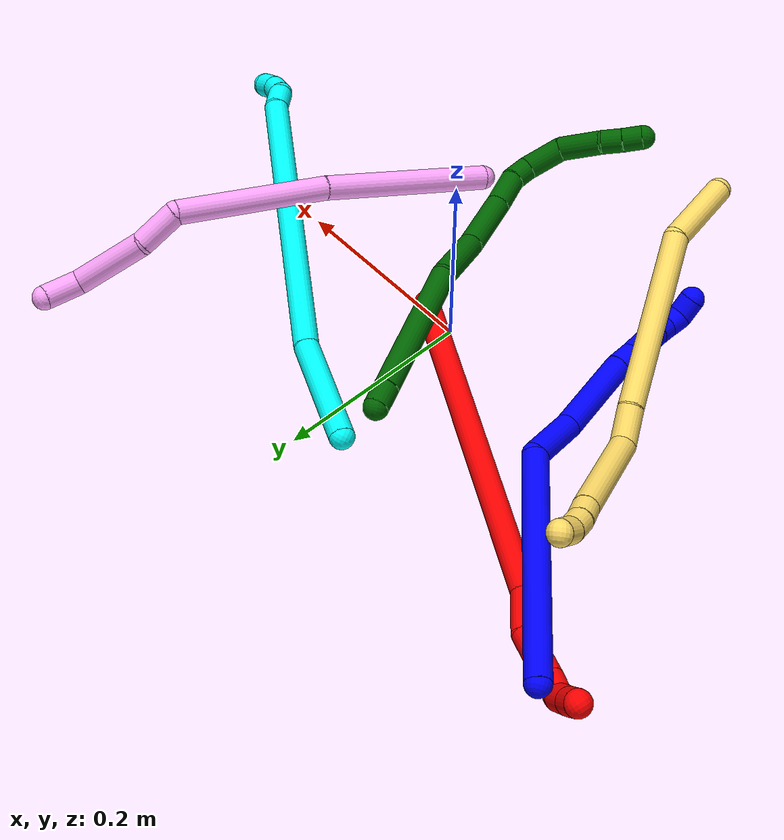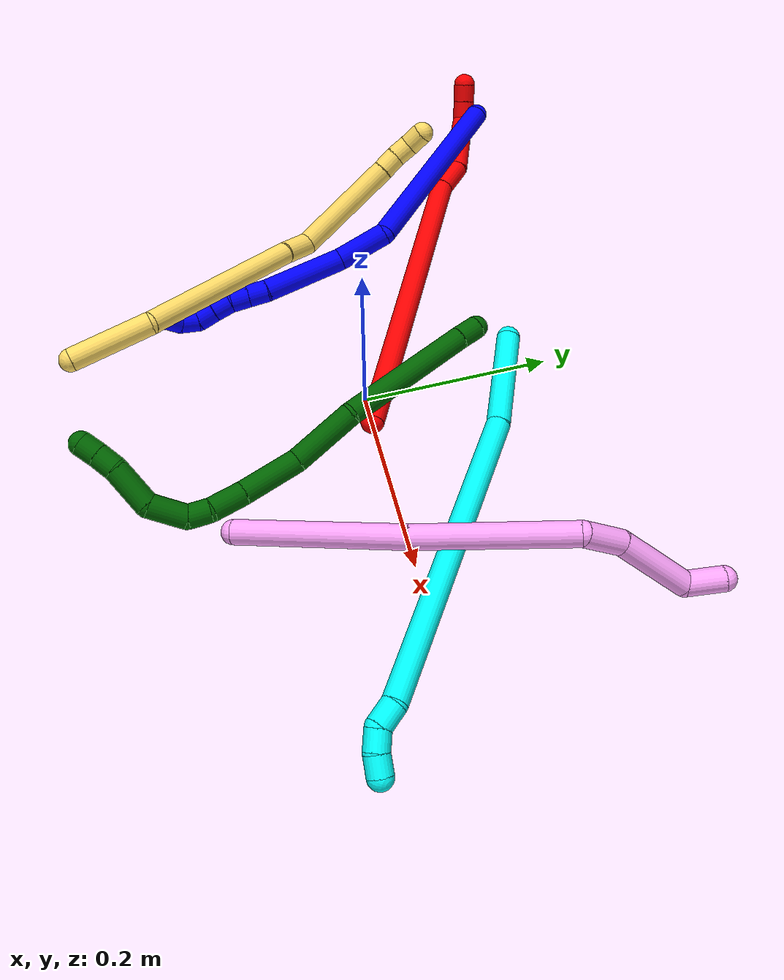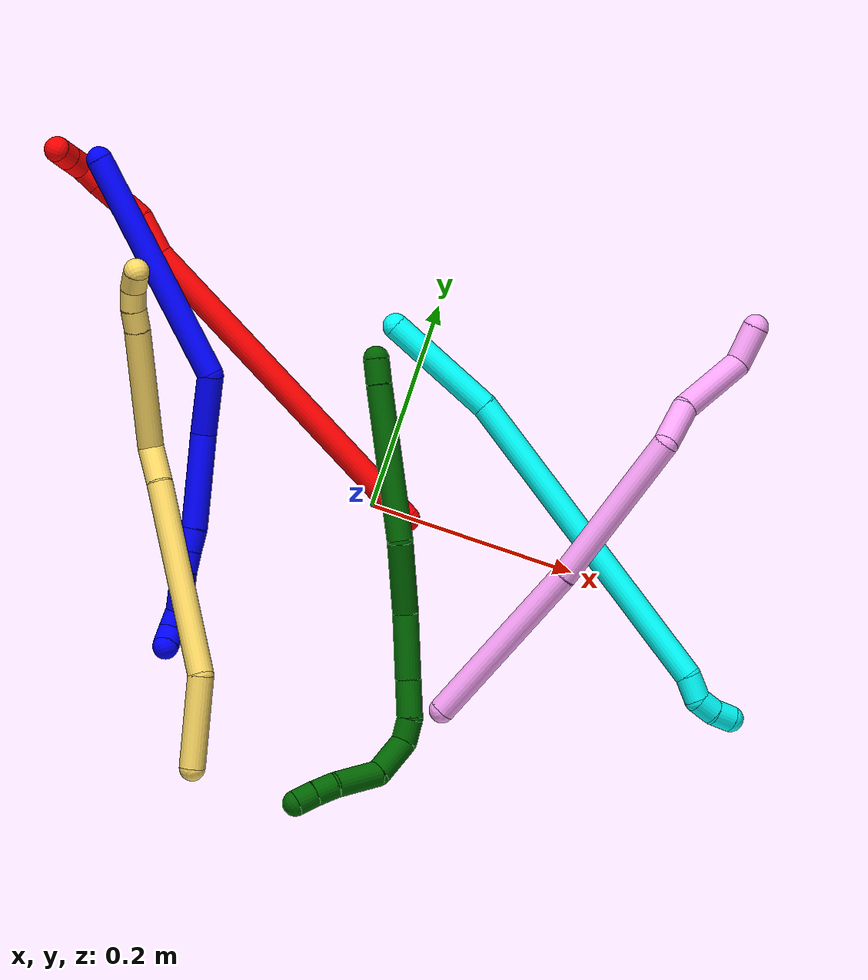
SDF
<sdf version="1.7">
 <world name="default">
  <plugin name="TubeGeneratorPlugin" filename="libtube_generator_plugin.so"/>
  <model name="photoneo_s_sensor">
   <static>1</static>
   <pose>0 0 2 1.57079 1.57079 3.14159</pose>
   <link name="link">
    <inertial><mass>0.1</mass></inertial>
    <sensor name="sensor" type="depth">
     <update_rate>30</update_rate>
     <camera>
      <horizontal_fov>1.22</horizontal_fov>
      <image><width>1920</width><height>1200</height><format>B8G8R8</format></image>
      <clip><near>0.1</near><far>4</far></clip>
      <depth_camera><output>points</output></depth_camera>
     </camera>
     <plugin name="camera_plugin" filename="libgazebo_ros_depth_camera.so">
      <baseline>0.2</baseline>
      <alwaysOn>1</alwaysOn>
      <updateRate>0.0</updateRate>
      <cameraName>camera_ir</cameraName>
      <imageTopicName>/camera/color/image_raw</imageTopicName>
      <cameraInfoTopicName>/camera/color/camera_info</cameraInfoTopicName>
      <depthImageTopicName>/camera/depth/image_raw</depthImageTopicName>
      <depthImageCameraInfoTopicName>/camera/depth/camera_info</depthImageCameraInfoTopicName>
      <pointCloudTopicName>/camera/depth/points</pointCloudTopicName>
      <frameName>fr_optical</frameName>
      <pointCloudCutoff>0.1</pointCloudCutoff>
      <pointCloudCutoffMax>2.0</pointCloudCutoffMax>
      <distortionK1>0</distortionK1>
      <distortionK2>0</distortionK2>
      <distortionK3>0</distortionK3>
      <distortionT1>0</distortionT1>
      <distortionT2>0</distortionT2>
      <CxPrime>0</CxPrime>
      <Cx>0</Cx>
      <Cy>0</Cy>
      <focalLength>0</focalLength>
      <hackBaseline>0</hackBaseline>
     </plugin>
    </sensor>
   </link>
  </model>
  <gravity>0 0 -9.8</gravity>
  <magnetic_field>6e-06 2.3e-05 -4.2e-05</magnetic_field>
  <atmosphere type="adiabatic"/>
  <physics name="default_physics" default="0" type="ode">
   <max_step_size>0.003</max_step_size>
   <real_time_factor>1</real_time_factor>
   <real_time_update_rate>1000</real_time_update_rate>
   <max_contacts>10000</max_contacts>
   <ode>
    <solver>
     <type>quick</type>
     <iters>100</iters>
     <sor>1.3</sor>
     <use_dynamic_moi_rescaling>0</use_dynamic_moi_rescaling>
    </solver>
    <constraints>
     <contact_max_correcting_vel>0</contact_max_correcting_vel>
     <contact_surface_layer>0.001</contact_surface_layer>
     <cfm>0</cfm>
     <erp>0.2</erp>
    </constraints>
   </ode>
  </physics>
  <scene><ambient>0.4 0.4 0.4 1</ambient><background>0.7 0.7 0.7 1</background><shadows>0</shadows></scene>
  <audio><device>default</device></audio>
  <spherical_coordinates>
   <surface_model>EARTH_WGS84</surface_model>
   <latitude_deg>0</latitude_deg>
   <longitude_deg>0</longitude_deg>
   <elevation>0</elevation>
   <heading_deg>0</heading_deg>
  </spherical_coordinates>
  <model name="bin">
   <static>1</static>
   <link name="bottom">
    <collision name="collision-bottom">
     <pose>0 0 -0.01 0 -0 0</pose>
     <geometry><box><size>0.8 0.6 0.02</size></box></geometry>
     <surface>
      <friction><ode><mu>100</mu><mu2>100</mu2></ode></friction>
      <contact><collide_bitmask>65535</collide_bitmask></contact>
     </surface>
    </collision>
   </link>
   <link name="west_wall">
    <collision name="collision-west_wall">
     <pose>-0.41 0 0.1 0 -0 0</pose>
     <geometry><box><size>0.02 0.6 0.2</size></box></geometry>
     <surface>
      <friction><ode><mu>100</mu><mu2>100</mu2></ode></friction>
      <contact><collide_bitmask>65535</collide_bitmask></contact>
     </surface>
    </collision>
   </link>
   <link name="east_wall">
    <collision name="collision-east_wall">
     <pose>0.41 0 0.1 0 -0 0</pose>
     <geometry><box><size>0.02 0.6 0.2</size></box></geometry>
     <surface>
      <friction><ode><mu>100</mu><mu2>100</mu2></ode></friction>
      <contact><collide_bitmask>65535</collide_bitmask></contact>
     </surface>
    </collision>
   </link>
   <link name="south_wall">
    <collision name="collision-south_wall">
     <pose>0 -0.31 0.1 0 -0 0</pose>
     <geometry><box><size>0.8 0.02 0.2</size></box></geometry>
     <surface>
      <friction><ode><mu>100</mu><mu2>100</mu2></ode></friction>
      <contact><collide_bitmask>65535</collide_bitmask></contact>
     </surface>
    </collision>
   </link>
   <link name="north_wall">
    <collision name="collision-north_wall">
     <pose>0 0.31 0.1 0 -0 0</pose>
     <geometry><box><size>0.8 0.02 0.2</size></box></geometry>
     <surface>
      <friction><ode><mu>100</mu><mu2>100</mu2></ode></friction>
      <contact><collide_bitmask>65535</collide_bitmask></contact>
     </surface>
    </collision>
   </link>
  </model>
  <model name="1">
   <static>0</static>
   <link name="1">
    <collision name="collision-cylinder-e_1_1_4">
     <pose>-0.030855 0.01054 -0.109899 -3.04597 -0.272526 2.47012</pose>
     <geometry><cylinder><radius>0.0125</radius><length>0.229267</length></cylinder></geometry>
     <surface>
      <friction><ode><mu>1.16</mu><mu2>1.16</mu2><slip1>0</slip1><slip2>0</slip2></ode></friction>
      <contact><ode><kp>1e+06</kp><kd>1</kd><max_vel>0</max_vel><min_depth>0.001</min_depth></ode></contact>
     </surface>
    </collision>
    <visual name="visual-cylinder-e_1_1_4">
     <pose>-0.030855 0.01054 -0.109899 -3.04597 -0.272526 2.47012</pose>
     <geometry><cylinder><radius>0.0125</radius><length>0.229267</length></cylinder></geometry>
     <material><ambient>0 0 1 1</ambient></material>
    </visual>
    <collision name="collision-cylinder-e_2_4_5">
     <pose>-0.069274 0.005402 -0.242929 2.54591 -0.264331 -0.817378</pose>
     <geometry><cylinder><radius>0.0125</radius><length>0.0579</length></cylinder></geometry>
     <surface>
      <friction><ode><mu>1.16</mu><mu2>1.16</mu2><slip1>0</slip1><slip2>0</slip2></ode></friction>
      <contact><ode><kp>1e+06</kp><kd>1</kd><max_vel>0</max_vel><min_depth>0.001</min_depth></ode></contact>
     </surface>
    </collision>
    <visual name="visual-cylinder-e_2_4_5">
     <pose>-0.069274 0.005402 -0.242929 2.54591 -0.264331 -0.817378</pose>
     <geometry><cylinder><radius>0.0125</radius><length>0.0579</length></cylinder></geometry>
     <material><ambient>0 0 1 1</ambient></material>
    </visual>
    <collision name="collision-cylinder-e_3_5_6">
     <pose>-0.08016 -0.030184 -0.306584 2.68498 -0.07344 -0.313611</pose>
     <geometry><cylinder><radius>0.0125</radius><length>0.090541</length></cylinder></geometry>
     <surface>
      <friction><ode><mu>1.16</mu><mu2>1.16</mu2><slip1>0</slip1><slip2>0</slip2></ode></friction>
      <contact><ode><kp>1e+06</kp><kd>1</kd><max_vel>0</max_vel><min_depth>0.001</min_depth></ode></contact>
     </surface>
    </collision>
    <visual name="visual-cylinder-e_3_5_6">
     <pose>-0.08016 -0.030184 -0.306584 2.68498 -0.07344 -0.313611</pose>
     <geometry><cylinder><radius>0.0125</radius><length>0.090541</length></cylinder></geometry>
     <material><ambient>0 0 1 1</ambient></material>
    </visual>
    <collision name="collision-cylinder-e_4_6_7">
     <pose>-0.083587 -0.056241 -0.356137 2.54366 -0.009657 -0.031332</pose>
     <geometry><cylinder><radius>0.0125</radius><length>0.021853</length></cylinder></geometry>
     <surface>
      <friction><ode><mu>1.16</mu><mu2>1.16</mu2><slip1>0</slip1><slip2>0</slip2></ode></friction>
      <contact><ode><kp>1e+06</kp><kd>1</kd><max_vel>0</max_vel><min_depth>0.001</min_depth></ode></contact>
     </surface>
    </collision>
    <visual name="visual-cylinder-e_4_6_7">
     <pose>-0.083587 -0.056241 -0.356137 2.54366 -0.009657 -0.031332</pose>
     <geometry><cylinder><radius>0.0125</radius><length>0.021853</length></cylinder></geometry>
     <material><ambient>0 0 1 1</ambient></material>
    </visual>
    <collision name="collision-cylinder-e_5_7_8">
     <pose>-0.08362 -0.06774 -0.373766 2.58513 0.00721 0.025239</pose>
     <geometry><cylinder><radius>0.0125</radius><length>0.020252</length></cylinder></geometry>
     <surface>
      <friction><ode><mu>1.16</mu><mu2>1.16</mu2><slip1>0</slip1><slip2>0</slip2></ode></friction>
      <contact><ode><kp>1e+06</kp><kd>1</kd><max_vel>0</max_vel><min_depth>0.001</min_depth></ode></contact>
     </surface>
    </collision>
    <visual name="visual-cylinder-e_5_7_8">
     <pose>-0.08362 -0.06774 -0.373766 2.58513 0.00721 0.025239</pose>
     <geometry><cylinder><radius>0.0125</radius><length>0.020252</length></cylinder></geometry>
     <material><ambient>0 0 1 1</ambient></material>
    </visual>
    <collision name="collision-cylinder-e_6_8_9">
     <pose>-0.086012 -0.07863 -0.390415 2.53872 -0.247127 -0.760083</pose>
     <geometry><cylinder><radius>0.0125</radius><length>0.020162</length></cylinder></geometry>
     <surface>
      <friction><ode><mu>1.16</mu><mu2>1.16</mu2><slip1>0</slip1><slip2>0</slip2></ode></friction>
      <contact><ode><kp>1e+06</kp><kd>1</kd><max_vel>0</max_vel><min_depth>0.001</min_depth></ode></contact>
     </surface>
    </collision>
    <visual name="visual-cylinder-e_6_8_9">
     <pose>-0.086012 -0.07863 -0.390415 2.53872 -0.247127 -0.760083</pose>
     <geometry><cylinder><radius>0.0125</radius><length>0.020162</length></cylinder></geometry>
     <material><ambient>0 0 1 1</ambient></material>
    </visual>
    <collision name="collision-cylinder-e_7_9_10">
     <pose>-0.091453 -0.089787 -0.406204 2.51383 -0.301664 -0.875786</pose>
     <geometry><cylinder><radius>0.0125</radius><length>0.020023</length></cylinder></geometry>
     <surface>
      <friction><ode><mu>1.16</mu><mu2>1.16</mu2><slip1>0</slip1><slip2>0</slip2></ode></friction>
      <contact><ode><kp>1e+06</kp><kd>1</kd><max_vel>0</max_vel><min_depth>0.001</min_depth></ode></contact>
     </surface>
    </collision>
    <visual name="visual-cylinder-e_7_9_10">
     <pose>-0.091453 -0.089787 -0.406204 2.51383 -0.301664 -0.875786</pose>
     <geometry><cylinder><radius>0.0125</radius><length>0.020023</length></cylinder></geometry>
     <material><ambient>0 0 1 1</ambient></material>
    </visual>
    <collision name="collision-cylinder-e_8_10_11">
     <pose>-0.09275 -0.101251 -0.421877 2.50646 0.168506 0.50299</pose>
     <geometry><cylinder><radius>0.0125</radius><length>0.020001</length></cylinder></geometry>
     <surface>
      <friction><ode><mu>1.16</mu><mu2>1.16</mu2><slip1>0</slip1><slip2>0</slip2></ode></friction>
      <contact><ode><kp>1e+06</kp><kd>1</kd><max_vel>0</max_vel><min_depth>0.001</min_depth></ode></contact>
     </surface>
    </collision>
    <visual name="visual-cylinder-e_8_10_11">
     <pose>-0.09275 -0.101251 -0.421877 2.50646 0.168506 0.50299</pose>
     <geometry><cylinder><radius>0.0125</radius><length>0.020001</length></cylinder></geometry>
     <material><ambient>0 0 1 1</ambient></material>
    </visual>
    <collision name="collision-cylinder-e_9_11_2">
     <pose>-0.084808 -0.108947 -0.437385 2.90229 0.677021 2.48345</pose>
     <geometry><cylinder><radius>0.0125</radius><length>0.020001</length></cylinder></geometry>
     <surface>
      <friction><ode><mu>1.16</mu><mu2>1.16</mu2><slip1>0</slip1><slip2>0</slip2></ode></friction>
      <contact><ode><kp>1e+06</kp><kd>1</kd><max_vel>0</max_vel><min_depth>0.001</min_depth></ode></contact>
     </surface>
    </collision>
    <visual name="visual-cylinder-e_9_11_2">
     <pose>-0.084808 -0.108947 -0.437385 2.90229 0.677021 2.48345</pose>
     <geometry><cylinder><radius>0.0125</radius><length>0.020001</length></cylinder></geometry>
     <material><ambient>0 0 1 1</ambient></material>
    </visual>
    <collision name="collision-sphere-2">
     <pose>-0.078543 -0.110795 -0.444958 0 -0 0</pose>
     <geometry><sphere><radius>0.0125</radius></sphere></geometry>
     <surface>
      <friction><ode><mu>1.16</mu><mu2>1.16</mu2><slip1>0</slip1><slip2>0</slip2></ode></friction>
      <contact><ode><kp>1e+06</kp><kd>1</kd><max_vel>0</max_vel><min_depth>0.001</min_depth></ode></contact>
     </surface>
    </collision>
    <visual name="visual-sphere-2">
     <pose>-0.078543 -0.110795 -0.444958 0 -0 0</pose>
     <geometry><sphere><radius>0.0125</radius></sphere></geometry>
     <material><ambient>0 0 1 1</ambient></material>
    </visual>
    <collision name="collision-sphere-11">
     <pose>-0.091073 -0.1071 -0.429813 0 -0 0</pose>
     <geometry><sphere><radius>0.0125</radius></sphere></geometry>
     <surface>
      <friction><ode><mu>1.16</mu><mu2>1.16</mu2><slip1>0</slip1><slip2>0</slip2></ode></friction>
      <contact><ode><kp>1e+06</kp><kd>1</kd><max_vel>0</max_vel><min_depth>0.001</min_depth></ode></contact>
     </surface>
    </collision>
    <visual name="visual-sphere-11">
     <pose>-0.091073 -0.1071 -0.429813 0 -0 0</pose>
     <geometry><sphere><radius>0.0125</radius></sphere></geometry>
     <material><ambient>0 0 1 1</ambient></material>
    </visual>
    <collision name="collision-sphere-10">
     <pose>-0.094428 -0.095402 -0.413941 0 -0 0</pose>
     <geometry><sphere><radius>0.0125</radius></sphere></geometry>
     <surface>
      <friction><ode><mu>1.16</mu><mu2>1.16</mu2><slip1>0</slip1><slip2>0</slip2></ode></friction>
      <contact><ode><kp>1e+06</kp><kd>1</kd><max_vel>0</max_vel><min_depth>0.001</min_depth></ode></contact>
     </surface>
    </collision>
    <visual name="visual-sphere-10">
     <pose>-0.094428 -0.095402 -0.413941 0 -0 0</pose>
     <geometry><sphere><radius>0.0125</radius></sphere></geometry>
     <material><ambient>0 0 1 1</ambient></material>
    </visual>
    <collision name="collision-sphere-9">
     <pose>-0.088478 -0.084173 -0.398467 0 -0 0</pose>
     <geometry><sphere><radius>0.0125</radius></sphere></geometry>
     <surface>
      <friction><ode><mu>1.16</mu><mu2>1.16</mu2><slip1>0</slip1><slip2>0</slip2></ode></friction>
      <contact><ode><kp>1e+06</kp><kd>1</kd><max_vel>0</max_vel><min_depth>0.001</min_depth></ode></contact>
     </surface>
    </collision>
    <visual name="visual-sphere-9">
     <pose>-0.088478 -0.084173 -0.398467 0 -0 0</pose>
     <geometry><sphere><radius>0.0125</radius></sphere></geometry>
     <material><ambient>0 0 1 1</ambient></material>
    </visual>
    <collision name="collision-sphere-4">
     <pose>-0.061711 0.021081 -0.219797 0 -0 0</pose>
     <geometry><sphere><radius>0.0125</radius></sphere></geometry>
     <surface>
      <friction><ode><mu>1.16</mu><mu2>1.16</mu2><slip1>0</slip1><slip2>0</slip2></ode></friction>
      <contact><ode><kp>1e+06</kp><kd>1</kd><max_vel>0</max_vel><min_depth>0.001</min_depth></ode></contact>
     </surface>
    </collision>
    <visual name="visual-sphere-4">
     <pose>-0.061711 0.021081 -0.219797 0 -0 0</pose>
     <geometry><sphere><radius>0.0125</radius></sphere></geometry>
     <material><ambient>0 0 1 1</ambient></material>
    </visual>
    <collision name="collision-sphere-1">
     <geometry><sphere><radius>0.0125</radius></sphere></geometry>
     <surface>
      <friction><ode><mu>1.16</mu><mu2>1.16</mu2><slip1>0</slip1><slip2>0</slip2></ode></friction>
      <contact><ode><kp>1e+06</kp><kd>1</kd><max_vel>0</max_vel><min_depth>0.001</min_depth></ode></contact>
     </surface>
    </collision>
    <visual name="visual-sphere-1">
     <geometry><sphere><radius>0.0125</radius></sphere></geometry>
     <material><ambient>0 0 1 1</ambient></material>
    </visual>
    <collision name="collision-sphere-8">
     <pose>-0.083547 -0.073088 -0.382364 0 -0 0</pose>
     <geometry><sphere><radius>0.0125</radius></sphere></geometry>
     <surface>
      <friction><ode><mu>1.16</mu><mu2>1.16</mu2><slip1>0</slip1><slip2>0</slip2></ode></friction>
      <contact><ode><kp>1e+06</kp><kd>1</kd><max_vel>0</max_vel><min_depth>0.001</min_depth></ode></contact>
     </surface>
    </collision>
    <visual name="visual-sphere-8">
     <pose>-0.083547 -0.073088 -0.382364 0 -0 0</pose>
     <geometry><sphere><radius>0.0125</radius></sphere></geometry>
     <material><ambient>0 0 1 1</ambient></material>
    </visual>
    <collision name="collision-sphere-5">
     <pose>-0.076838 -0.010277 -0.266061 0 -0 0</pose>
     <geometry><sphere><radius>0.0125</radius></sphere></geometry>
     <surface>
      <friction><ode><mu>1.16</mu><mu2>1.16</mu2><slip1>0</slip1><slip2>0</slip2></ode></friction>
      <contact><ode><kp>1e+06</kp><kd>1</kd><max_vel>0</max_vel><min_depth>0.001</min_depth></ode></contact>
     </surface>
    </collision>
    <visual name="visual-sphere-5">
     <pose>-0.076838 -0.010277 -0.266061 0 -0 0</pose>
     <geometry><sphere><radius>0.0125</radius></sphere></geometry>
     <material><ambient>0 0 1 1</ambient></material>
    </visual>
    <collision name="collision-sphere-6">
     <pose>-0.083481 -0.05009 -0.347107 0 -0 0</pose>
     <geometry><sphere><radius>0.0125</radius></sphere></geometry>
     <surface>
      <friction><ode><mu>1.16</mu><mu2>1.16</mu2><slip1>0</slip1><slip2>0</slip2></ode></friction>
      <contact><ode><kp>1e+06</kp><kd>1</kd><max_vel>0</max_vel><min_depth>0.001</min_depth></ode></contact>
     </surface>
    </collision>
    <visual name="visual-sphere-6">
     <pose>-0.083481 -0.05009 -0.347107 0 -0 0</pose>
     <geometry><sphere><radius>0.0125</radius></sphere></geometry>
     <material><ambient>0 0 1 1</ambient></material>
    </visual>
    <collision name="collision-sphere-7">
     <pose>-0.083693 -0.062391 -0.365168 0 -0 0</pose>
     <geometry><sphere><radius>0.0125</radius></sphere></geometry>
     <surface>
      <friction><ode><mu>1.16</mu><mu2>1.16</mu2><slip1>0</slip1><slip2>0</slip2></ode></friction>
      <contact><ode><kp>1e+06</kp><kd>1</kd><max_vel>0</max_vel><min_depth>0.001</min_depth></ode></contact>
     </surface>
    </collision>
    <visual name="visual-sphere-7">
     <pose>-0.083693 -0.062391 -0.365168 0 -0 0</pose>
     <geometry><sphere><radius>0.0125</radius></sphere></geometry>
     <material><ambient>0 0 1 1</ambient></material>
    </visual>
    <inertial>
     <pose>-0.057959 -0.020383 -0.231126 0 -0 0</pose>
     <mass>0.5</mass>
     <inertia>
      <ixx>-0.000117</ixx>
      <ixy>0</ixy>
      <ixz>0</ixz>
      <iyy>0.001303</iyy>
      <iyz>0</iyz>
      <izz>0.000197</izz>
     </inertia>
    </inertial>
   </link>
   <pose>-0.348402 0.228598 0.042811 2.06126 -1.07689 -2.9799</pose>
  </model>
  <model name="2">
   <static>0</static>
   <link name="2">
    <collision name="collision-cylinder-e_1_1_4">
     <pose>-0.08825 0.030583 0.14419 -0.209003 -0.539477 0.057979</pose>
     <geometry><cylinder><radius>0.0125</radius><length>0.343594</length></cylinder></geometry>
     <surface>
      <friction><ode><mu>1.16</mu><mu2>1.16</mu2><slip1>0</slip1><slip2>0</slip2></ode></friction>
      <contact><ode><kp>1e+06</kp><kd>1</kd><max_vel>0</max_vel><min_depth>0.001</min_depth></ode></contact>
     </surface>
    </collision>
    <visual name="visual-cylinder-e_1_1_4">
     <pose>-0.08825 0.030583 0.14419 -0.209003 -0.539477 0.057979</pose>
     <geometry><cylinder><radius>0.0125</radius><length>0.343594</length></cylinder></geometry>
     <material><ambient>1 0 0 1</ambient></material>
    </visual>
    <collision name="collision-cylinder-e_2_4_5">
     <pose>-0.189806 0.060665 0.30329 0.033537 -0.728331 -0.012784</pose>
     <geometry><cylinder><radius>0.0125</radius><length>0.03998</length></cylinder></geometry>
     <surface>
      <friction><ode><mu>1.16</mu><mu2>1.16</mu2><slip1>0</slip1><slip2>0</slip2></ode></friction>
      <contact><ode><kp>1e+06</kp><kd>1</kd><max_vel>0</max_vel><min_depth>0.001</min_depth></ode></contact>
     </surface>
    </collision>
    <visual name="visual-cylinder-e_2_4_5">
     <pose>-0.189806 0.060665 0.30329 0.033537 -0.728331 -0.012784</pose>
     <geometry><cylinder><radius>0.0125</radius><length>0.03998</length></cylinder></geometry>
     <material><ambient>1 0 0 1</ambient></material>
    </visual>
    <collision name="collision-cylinder-e_3_5_6">
     <pose>-0.215678 0.069676 0.338665 -0.435058 -0.508084 0.114654</pose>
     <geometry><cylinder><radius>0.0125</radius><length>0.05166</length></cylinder></geometry>
     <surface>
      <friction><ode><mu>1.16</mu><mu2>1.16</mu2><slip1>0</slip1><slip2>0</slip2></ode></friction>
      <contact><ode><kp>1e+06</kp><kd>1</kd><max_vel>0</max_vel><min_depth>0.001</min_depth></ode></contact>
     </surface>
    </collision>
    <visual name="visual-cylinder-e_3_5_6">
     <pose>-0.215678 0.069676 0.338665 -0.435058 -0.508084 0.114654</pose>
     <geometry><cylinder><radius>0.0125</radius><length>0.05166</length></cylinder></geometry>
     <material><ambient>1 0 0 1</ambient></material>
    </visual>
    <collision name="collision-cylinder-e_4_6_7">
     <pose>-0.234068 0.083113 0.367205 -0.452452 -0.575383 0.136002</pose>
     <geometry><cylinder><radius>0.0125</radius><length>0.021404</length></cylinder></geometry>
     <surface>
      <friction><ode><mu>1.16</mu><mu2>1.16</mu2><slip1>0</slip1><slip2>0</slip2></ode></friction>
      <contact><ode><kp>1e+06</kp><kd>1</kd><max_vel>0</max_vel><min_depth>0.001</min_depth></ode></contact>
     </surface>
    </collision>
    <visual name="visual-cylinder-e_4_6_7">
     <pose>-0.234068 0.083113 0.367205 -0.452452 -0.575383 0.136002</pose>
     <geometry><cylinder><radius>0.0125</radius><length>0.021404</length></cylinder></geometry>
     <material><ambient>1 0 0 1</ambient></material>
    </visual>
    <collision name="collision-cylinder-e_5_7_8">
     <pose>-0.245954 0.09633 0.378395 -1.24731 -0.554013 0.40353</pose>
     <geometry><cylinder><radius>0.0125</radius><length>0.023048</length></cylinder></geometry>
     <surface>
      <friction><ode><mu>1.16</mu><mu2>1.16</mu2><slip1>0</slip1><slip2>0</slip2></ode></friction>
      <contact><ode><kp>1e+06</kp><kd>1</kd><max_vel>0</max_vel><min_depth>0.001</min_depth></ode></contact>
     </surface>
    </collision>
    <visual name="visual-cylinder-e_5_7_8">
     <pose>-0.245954 0.09633 0.378395 -1.24731 -0.554013 0.40353</pose>
     <geometry><cylinder><radius>0.0125</radius><length>0.023048</length></cylinder></geometry>
     <material><ambient>1 0 0 1</ambient></material>
    </visual>
    <collision name="collision-cylinder-e_6_8_2">
     <pose>-0.257466 0.113974 0.383437 -1.34416 -0.566284 0.454985</pose>
     <geometry><cylinder><radius>0.0125</radius><length>0.020315</length></cylinder></geometry>
     <surface>
      <friction><ode><mu>1.16</mu><mu2>1.16</mu2><slip1>0</slip1><slip2>0</slip2></ode></friction>
      <contact><ode><kp>1e+06</kp><kd>1</kd><max_vel>0</max_vel><min_depth>0.001</min_depth></ode></contact>
     </surface>
    </collision>
    <visual name="visual-cylinder-e_6_8_2">
     <pose>-0.257466 0.113974 0.383437 -1.34416 -0.566284 0.454985</pose>
     <geometry><cylinder><radius>0.0125</radius><length>0.020315</length></cylinder></geometry>
     <material><ambient>1 0 0 1</ambient></material>
    </visual>
    <collision name="collision-sphere-2">
     <pose>-0.262916 0.122327 0.385363 0 -0 0</pose>
     <geometry><sphere><radius>0.0125</radius></sphere></geometry>
     <surface>
      <friction><ode><mu>1.16</mu><mu2>1.16</mu2><slip1>0</slip1><slip2>0</slip2></ode></friction>
      <contact><ode><kp>1e+06</kp><kd>1</kd><max_vel>0</max_vel><min_depth>0.001</min_depth></ode></contact>
     </surface>
    </collision>
    <visual name="visual-sphere-2">
     <pose>-0.262916 0.122327 0.385363 0 -0 0</pose>
     <geometry><sphere><radius>0.0125</radius></sphere></geometry>
     <material><ambient>1 0 0 1</ambient></material>
    </visual>
    <collision name="collision-sphere-4">
     <pose>-0.1765 0.061166 0.28838 0 -0 0</pose>
     <geometry><sphere><radius>0.0125</radius></sphere></geometry>
     <surface>
      <friction><ode><mu>1.16</mu><mu2>1.16</mu2><slip1>0</slip1><slip2>0</slip2></ode></friction>
      <contact><ode><kp>1e+06</kp><kd>1</kd><max_vel>0</max_vel><min_depth>0.001</min_depth></ode></contact>
     </surface>
    </collision>
    <visual name="visual-sphere-4">
     <pose>-0.1765 0.061166 0.28838 0 -0 0</pose>
     <geometry><sphere><radius>0.0125</radius></sphere></geometry>
     <material><ambient>1 0 0 1</ambient></material>
    </visual>
    <collision name="collision-sphere-1">
     <geometry><sphere><radius>0.0125</radius></sphere></geometry>
     <surface>
      <friction><ode><mu>1.16</mu><mu2>1.16</mu2><slip1>0</slip1><slip2>0</slip2></ode></friction>
      <contact><ode><kp>1e+06</kp><kd>1</kd><max_vel>0</max_vel><min_depth>0.001</min_depth></ode></contact>
     </surface>
    </collision>
    <visual name="visual-sphere-1">
     <geometry><sphere><radius>0.0125</radius></sphere></geometry>
     <material><ambient>1 0 0 1</ambient></material>
    </visual>
    <collision name="collision-sphere-8">
     <pose>-0.252017 0.105622 0.381511 0 -0 0</pose>
     <geometry><sphere><radius>0.0125</radius></sphere></geometry>
     <surface>
      <friction><ode><mu>1.16</mu><mu2>1.16</mu2><slip1>0</slip1><slip2>0</slip2></ode></friction>
      <contact><ode><kp>1e+06</kp><kd>1</kd><max_vel>0</max_vel><min_depth>0.001</min_depth></ode></contact>
     </surface>
    </collision>
    <visual name="visual-sphere-8">
     <pose>-0.252017 0.105622 0.381511 0 -0 0</pose>
     <geometry><sphere><radius>0.0125</radius></sphere></geometry>
     <material><ambient>1 0 0 1</ambient></material>
    </visual>
    <collision name="collision-sphere-5">
     <pose>-0.203111 0.060165 0.3182 0 -0 0</pose>
     <geometry><sphere><radius>0.0125</radius></sphere></geometry>
     <surface>
      <friction><ode><mu>1.16</mu><mu2>1.16</mu2><slip1>0</slip1><slip2>0</slip2></ode></friction>
      <contact><ode><kp>1e+06</kp><kd>1</kd><max_vel>0</max_vel><min_depth>0.001</min_depth></ode></contact>
     </surface>
    </collision>
    <visual name="visual-sphere-5">
     <pose>-0.203111 0.060165 0.3182 0 -0 0</pose>
     <geometry><sphere><radius>0.0125</radius></sphere></geometry>
     <material><ambient>1 0 0 1</ambient></material>
    </visual>
    <collision name="collision-sphere-6">
     <pose>-0.228244 0.079187 0.35913 0 -0 0</pose>
     <geometry><sphere><radius>0.0125</radius></sphere></geometry>
     <surface>
      <friction><ode><mu>1.16</mu><mu2>1.16</mu2><slip1>0</slip1><slip2>0</slip2></ode></friction>
      <contact><ode><kp>1e+06</kp><kd>1</kd><max_vel>0</max_vel><min_depth>0.001</min_depth></ode></contact>
     </surface>
    </collision>
    <visual name="visual-sphere-6">
     <pose>-0.228244 0.079187 0.35913 0 -0 0</pose>
     <geometry><sphere><radius>0.0125</radius></sphere></geometry>
     <material><ambient>1 0 0 1</ambient></material>
    </visual>
    <collision name="collision-sphere-7">
     <pose>-0.239891 0.087038 0.37528 0 -0 0</pose>
     <geometry><sphere><radius>0.0125</radius></sphere></geometry>
     <surface>
      <friction><ode><mu>1.16</mu><mu2>1.16</mu2><slip1>0</slip1><slip2>0</slip2></ode></friction>
      <contact><ode><kp>1e+06</kp><kd>1</kd><max_vel>0</max_vel><min_depth>0.001</min_depth></ode></contact>
     </surface>
    </collision>
    <visual name="visual-sphere-7">
     <pose>-0.239891 0.087038 0.37528 0 -0 0</pose>
     <geometry><sphere><radius>0.0125</radius></sphere></geometry>
     <material><ambient>1 0 0 1</ambient></material>
    </visual>
    <inertial>
     <pose>-0.129923 0.045695 0.207068 0 -0 0</pose>
     <mass>0.5</mass>
     <inertia>
      <ixx>0.003079</ixx>
      <ixy>0</ixy>
      <ixz>0</ixz>
      <iyy>0.003539</iyy>
      <iyz>0</iyz>
      <izz>0.001175</izz>
     </inertia>
    </inertial>
   </link>
   <pose>0.0356 -0.000872 0.011695 2.04548 0.424688 -1.46886</pose>
  </model>
  <model name="3">
   <static>0</static>
   <link name="3">
    <collision name="collision-cylinder-e_1_1_4">
     <pose>0.041297 -0.021447 0.032581 0.582167 0.813915 0.256839</pose>
     <geometry><cylinder><radius>0.0125</radius><length>0.113612</length></cylinder></geometry>
     <surface>
      <friction><ode><mu>1.16</mu><mu2>1.16</mu2><slip1>0</slip1><slip2>0</slip2></ode></friction>
      <contact><ode><kp>1e+06</kp><kd>1</kd><max_vel>0</max_vel><min_depth>0.001</min_depth></ode></contact>
     </surface>
    </collision>
    <visual name="visual-cylinder-e_1_1_4">
     <pose>0.041297 -0.021447 0.032581 0.582167 0.813915 0.256839</pose>
     <geometry><cylinder><radius>0.0125</radius><length>0.113612</length></cylinder></geometry>
     <material><ambient>0.003922 1 0.996078 1</ambient></material>
    </visual>
    <collision name="collision-cylinder-e_2_4_5">
     <pose>0.200299 -0.1264 0.134897 0.875019 0.824721 0.403647</pose>
     <geometry><cylinder><radius>0.0125</radius><length>0.320567</length></cylinder></geometry>
     <surface>
      <friction><ode><mu>1.16</mu><mu2>1.16</mu2><slip1>0</slip1><slip2>0</slip2></ode></friction>
      <contact><ode><kp>1e+06</kp><kd>1</kd><max_vel>0</max_vel><min_depth>0.001</min_depth></ode></contact>
     </surface>
    </collision>
    <visual name="visual-cylinder-e_2_4_5">
     <pose>0.200299 -0.1264 0.134897 0.875019 0.824721 0.403647</pose>
     <geometry><cylinder><radius>0.0125</radius><length>0.320567</length></cylinder></geometry>
     <material><ambient>0.003922 1 0.996078 1</ambient></material>
    </visual>
    <collision name="collision-cylinder-e_3_5_6">
     <pose>0.328121 -0.216691 0.206493 1.30316 0.963105 0.758558</pose>
     <geometry><cylinder><radius>0.0125</radius><length>0.024646</length></cylinder></geometry>
     <surface>
      <friction><ode><mu>1.16</mu><mu2>1.16</mu2><slip1>0</slip1><slip2>0</slip2></ode></friction>
      <contact><ode><kp>1e+06</kp><kd>1</kd><max_vel>0</max_vel><min_depth>0.001</min_depth></ode></contact>
     </surface>
    </collision>
    <visual name="visual-cylinder-e_3_5_6">
     <pose>0.328121 -0.216691 0.206493 1.30316 0.963105 0.758558</pose>
     <geometry><cylinder><radius>0.0125</radius><length>0.024646</length></cylinder></geometry>
     <material><ambient>0.003922 1 0.996078 1</ambient></material>
    </visual>
    <collision name="collision-cylinder-e_4_6_7">
     <pose>0.347513 -0.223948 0.213105 0.099025 1.09537 0.060429</pose>
     <geometry><cylinder><radius>0.0125</radius><length>0.020865</length></cylinder></geometry>
     <surface>
      <friction><ode><mu>1.16</mu><mu2>1.16</mu2><slip1>0</slip1><slip2>0</slip2></ode></friction>
      <contact><ode><kp>1e+06</kp><kd>1</kd><max_vel>0</max_vel><min_depth>0.001</min_depth></ode></contact>
     </surface>
    </collision>
    <visual name="visual-cylinder-e_4_6_7">
     <pose>0.347513 -0.223948 0.213105 0.099025 1.09537 0.060429</pose>
     <geometry><cylinder><radius>0.0125</radius><length>0.020865</length></cylinder></geometry>
     <material><ambient>0.003922 1 0.996078 1</ambient></material>
    </visual>
    <collision name="collision-cylinder-e_5_7_2">
     <pose>0.365086 -0.222529 0.223398 -0.328871 0.956288 -0.17157</pose>
     <geometry><cylinder><radius>0.0125</radius><length>0.020311</length></cylinder></geometry>
     <surface>
      <friction><ode><mu>1.16</mu><mu2>1.16</mu2><slip1>0</slip1><slip2>0</slip2></ode></friction>
      <contact><ode><kp>1e+06</kp><kd>1</kd><max_vel>0</max_vel><min_depth>0.001</min_depth></ode></contact>
     </surface>
    </collision>
    <visual name="visual-cylinder-e_5_7_2">
     <pose>0.365086 -0.222529 0.223398 -0.328871 0.956288 -0.17157</pose>
     <geometry><cylinder><radius>0.0125</radius><length>0.020311</length></cylinder></geometry>
     <material><ambient>0.003922 1 0.996078 1</ambient></material>
    </visual>
    <collision name="collision-sphere-2">
     <pose>0.373384 -0.220638 0.22894 0 -0 0</pose>
     <geometry><sphere><radius>0.0125</radius></sphere></geometry>
     <surface>
      <friction><ode><mu>1.16</mu><mu2>1.16</mu2><slip1>0</slip1><slip2>0</slip2></ode></friction>
      <contact><ode><kp>1e+06</kp><kd>1</kd><max_vel>0</max_vel><min_depth>0.001</min_depth></ode></contact>
     </surface>
    </collision>
    <visual name="visual-sphere-2">
     <pose>0.373384 -0.220638 0.22894 0 -0 0</pose>
     <geometry><sphere><radius>0.0125</radius></sphere></geometry>
     <material><ambient>0.003922 1 0.996078 1</ambient></material>
    </visual>
    <collision name="collision-sphere-7">
     <pose>0.356789 -0.224421 0.217857 0 -0 0</pose>
     <geometry><sphere><radius>0.0125</radius></sphere></geometry>
     <surface>
      <friction><ode><mu>1.16</mu><mu2>1.16</mu2><slip1>0</slip1><slip2>0</slip2></ode></friction>
      <contact><ode><kp>1e+06</kp><kd>1</kd><max_vel>0</max_vel><min_depth>0.001</min_depth></ode></contact>
     </surface>
    </collision>
    <visual name="visual-sphere-7">
     <pose>0.356789 -0.224421 0.217857 0 -0 0</pose>
     <geometry><sphere><radius>0.0125</radius></sphere></geometry>
     <material><ambient>0.003922 1 0.996078 1</ambient></material>
    </visual>
    <collision name="collision-sphere-6">
     <pose>0.338238 -0.223476 0.208354 0 -0 0</pose>
     <geometry><sphere><radius>0.0125</radius></sphere></geometry>
     <surface>
      <friction><ode><mu>1.16</mu><mu2>1.16</mu2><slip1>0</slip1><slip2>0</slip2></ode></friction>
      <contact><ode><kp>1e+06</kp><kd>1</kd><max_vel>0</max_vel><min_depth>0.001</min_depth></ode></contact>
     </surface>
    </collision>
    <visual name="visual-sphere-6">
     <pose>0.338238 -0.223476 0.208354 0 -0 0</pose>
     <geometry><sphere><radius>0.0125</radius></sphere></geometry>
     <material><ambient>0.003922 1 0.996078 1</ambient></material>
    </visual>
    <collision name="collision-sphere-5">
     <pose>0.318005 -0.209905 0.204632 0 -0 0</pose>
     <geometry><sphere><radius>0.0125</radius></sphere></geometry>
     <surface>
      <friction><ode><mu>1.16</mu><mu2>1.16</mu2><slip1>0</slip1><slip2>0</slip2></ode></friction>
      <contact><ode><kp>1e+06</kp><kd>1</kd><max_vel>0</max_vel><min_depth>0.001</min_depth></ode></contact>
     </surface>
    </collision>
    <visual name="visual-sphere-5">
     <pose>0.318005 -0.209905 0.204632 0 -0 0</pose>
     <geometry><sphere><radius>0.0125</radius></sphere></geometry>
     <material><ambient>0.003922 1 0.996078 1</ambient></material>
    </visual>
    <collision name="collision-sphere-1">
     <geometry><sphere><radius>0.0125</radius></sphere></geometry>
     <surface>
      <friction><ode><mu>1.16</mu><mu2>1.16</mu2><slip1>0</slip1><slip2>0</slip2></ode></friction>
      <contact><ode><kp>1e+06</kp><kd>1</kd><max_vel>0</max_vel><min_depth>0.001</min_depth></ode></contact>
     </surface>
    </collision>
    <visual name="visual-sphere-1">
     <geometry><sphere><radius>0.0125</radius></sphere></geometry>
     <material><ambient>0.003922 1 0.996078 1</ambient></material>
    </visual>
    <collision name="collision-sphere-4">
     <pose>0.082594 -0.042894 0.065162 0 -0 0</pose>
     <geometry><sphere><radius>0.0125</radius></sphere></geometry>
     <surface>
      <friction><ode><mu>1.16</mu><mu2>1.16</mu2><slip1>0</slip1><slip2>0</slip2></ode></friction>
      <contact><ode><kp>1e+06</kp><kd>1</kd><max_vel>0</max_vel><min_depth>0.001</min_depth></ode></contact>
     </surface>
    </collision>
    <visual name="visual-sphere-4">
     <pose>0.082594 -0.042894 0.065162 0 -0 0</pose>
     <geometry><sphere><radius>0.0125</radius></sphere></geometry>
     <material><ambient>0.003922 1 0.996078 1</ambient></material>
    </visual>
    <inertial>
     <pose>0.183308 -0.114978 0.122036 0 -0 0</pose>
     <mass>0.5</mass>
     <inertia>
      <ixx>0.002595</ixx>
      <ixy>0</ixy>
      <ixz>0</ixz>
      <iyy>0.003097</iyy>
      <iyz>0</iyz>
      <izz>-0.000618</izz>
     </inertia>
    </inertial>
   </link>
   <pose>-0.032733 0.169163 0.011843 -1.1128 0.676143 -0.76258</pose>
  </model>
  <model name="4">
   <static>0</static>
   <link name="4">
    <collision name="collision-cylinder-e_1_1_4">
     <pose>0.005916 0.087738 0.005238 -1.51116 0.06721 -0.063319</pose>
     <geometry><cylinder><radius>0.0125</radius><length>0.176186</length></cylinder></geometry>
     <surface>
      <friction><ode><mu>1.16</mu><mu2>1.16</mu2><slip1>0</slip1><slip2>0</slip2></ode></friction>
      <contact><ode><kp>1e+06</kp><kd>1</kd><max_vel>0</max_vel><min_depth>0.001</min_depth></ode></contact>
     </surface>
    </collision>
    <visual name="visual-cylinder-e_1_1_4">
     <pose>0.005916 0.087738 0.005238 -1.51116 0.06721 -0.063319</pose>
     <geometry><cylinder><radius>0.0125</radius><length>0.176186</length></cylinder></geometry>
     <material><ambient>1 0.65098 0.996078 1</ambient></material>
    </visual>
    <collision name="collision-cylinder-e_2_4_5">
     <pose>0.024514 0.254204 0.01518 -1.51113 0.159434 -0.150229</pose>
     <geometry><cylinder><radius>0.0125</radius><length>0.159763</length></cylinder></geometry>
     <surface>
      <friction><ode><mu>1.16</mu><mu2>1.16</mu2><slip1>0</slip1><slip2>0</slip2></ode></friction>
      <contact><ode><kp>1e+06</kp><kd>1</kd><max_vel>0</max_vel><min_depth>0.001</min_depth></ode></contact>
     </surface>
    </collision>
    <visual name="visual-cylinder-e_2_4_5">
     <pose>0.024514 0.254204 0.01518 -1.51113 0.159434 -0.150229</pose>
     <geometry><cylinder><radius>0.0125</radius><length>0.159763</length></cylinder></geometry>
     <material><ambient>1 0.65098 0.996078 1</ambient></material>
    </visual>
    <collision name="collision-cylinder-e_3_5_6">
     <pose>0.049765 0.347251 0.031425 -0.892405 0.599511 -0.293577</pose>
     <geometry><cylinder><radius>0.0125</radius><length>0.044552</length></cylinder></geometry>
     <surface>
      <friction><ode><mu>1.16</mu><mu2>1.16</mu2><slip1>0</slip1><slip2>0</slip2></ode></friction>
      <contact><ode><kp>1e+06</kp><kd>1</kd><max_vel>0</max_vel><min_depth>0.001</min_depth></ode></contact>
     </surface>
    </collision>
    <visual name="visual-cylinder-e_3_5_6">
     <pose>0.049765 0.347251 0.031425 -0.892405 0.599511 -0.293577</pose>
     <geometry><cylinder><radius>0.0125</radius><length>0.044552</length></cylinder></geometry>
     <material><ambient>1 0.65098 0.996078 1</ambient></material>
    </visual>
    <collision name="collision-cylinder-e_4_6_7">
     <pose>0.074828 0.386544 0.072162 -0.707625 0.314405 -0.11696</pose>
     <geometry><cylinder><radius>0.0125</radius><length>0.0808</length></cylinder></geometry>
     <surface>
      <friction><ode><mu>1.16</mu><mu2>1.16</mu2><slip1>0</slip1><slip2>0</slip2></ode></friction>
      <contact><ode><kp>1e+06</kp><kd>1</kd><max_vel>0</max_vel><min_depth>0.001</min_depth></ode></contact>
     </surface>
    </collision>
    <visual name="visual-cylinder-e_4_6_7">
     <pose>0.074828 0.386544 0.072162 -0.707625 0.314405 -0.11696</pose>
     <geometry><cylinder><radius>0.0125</radius><length>0.0808</length></cylinder></geometry>
     <material><ambient>1 0.65098 0.996078 1</ambient></material>
    </visual>
    <collision name="collision-cylinder-e_5_7_2">
     <pose>0.094824 0.429302 0.10272 -1.4943 0.398153 -0.369493</pose>
     <geometry><cylinder><radius>0.0125</radius><length>0.038699</length></cylinder></geometry>
     <surface>
      <friction><ode><mu>1.16</mu><mu2>1.16</mu2><slip1>0</slip1><slip2>0</slip2></ode></friction>
      <contact><ode><kp>1e+06</kp><kd>1</kd><max_vel>0</max_vel><min_depth>0.001</min_depth></ode></contact>
     </surface>
    </collision>
    <visual name="visual-cylinder-e_5_7_2">
     <pose>0.094824 0.429302 0.10272 -1.4943 0.398153 -0.369493</pose>
     <geometry><cylinder><radius>0.0125</radius><length>0.038699</length></cylinder></geometry>
     <material><ambient>1 0.65098 0.996078 1</ambient></material>
    </visual>
    <collision name="collision-sphere-2">
     <pose>0.102326 0.447086 0.104083 0 -0 0</pose>
     <geometry><sphere><radius>0.0125</radius></sphere></geometry>
     <surface>
      <friction><ode><mu>1.16</mu><mu2>1.16</mu2><slip1>0</slip1><slip2>0</slip2></ode></friction>
      <contact><ode><kp>1e+06</kp><kd>1</kd><max_vel>0</max_vel><min_depth>0.001</min_depth></ode></contact>
     </surface>
    </collision>
    <visual name="visual-sphere-2">
     <pose>0.102326 0.447086 0.104083 0 -0 0</pose>
     <geometry><sphere><radius>0.0125</radius></sphere></geometry>
     <material><ambient>1 0.65098 0.996078 1</ambient></material>
    </visual>
    <collision name="collision-sphere-7">
     <pose>0.087322 0.411518 0.101357 0 -0 0</pose>
     <geometry><sphere><radius>0.0125</radius></sphere></geometry>
     <surface>
      <friction><ode><mu>1.16</mu><mu2>1.16</mu2><slip1>0</slip1><slip2>0</slip2></ode></friction>
      <contact><ode><kp>1e+06</kp><kd>1</kd><max_vel>0</max_vel><min_depth>0.001</min_depth></ode></contact>
     </surface>
    </collision>
    <visual name="visual-sphere-7">
     <pose>0.087322 0.411518 0.101357 0 -0 0</pose>
     <geometry><sphere><radius>0.0125</radius></sphere></geometry>
     <material><ambient>1 0.65098 0.996078 1</ambient></material>
    </visual>
    <collision name="collision-sphere-6">
     <pose>0.062334 0.36157 0.042966 0 -0 0</pose>
     <geometry><sphere><radius>0.0125</radius></sphere></geometry>
     <surface>
      <friction><ode><mu>1.16</mu><mu2>1.16</mu2><slip1>0</slip1><slip2>0</slip2></ode></friction>
      <contact><ode><kp>1e+06</kp><kd>1</kd><max_vel>0</max_vel><min_depth>0.001</min_depth></ode></contact>
     </surface>
    </collision>
    <visual name="visual-sphere-6">
     <pose>0.062334 0.36157 0.042966 0 -0 0</pose>
     <geometry><sphere><radius>0.0125</radius></sphere></geometry>
     <material><ambient>1 0.65098 0.996078 1</ambient></material>
    </visual>
    <collision name="collision-sphere-5">
     <pose>0.037196 0.332932 0.019884 0 -0 0</pose>
     <geometry><sphere><radius>0.0125</radius></sphere></geometry>
     <surface>
      <friction><ode><mu>1.16</mu><mu2>1.16</mu2><slip1>0</slip1><slip2>0</slip2></ode></friction>
      <contact><ode><kp>1e+06</kp><kd>1</kd><max_vel>0</max_vel><min_depth>0.001</min_depth></ode></contact>
     </surface>
    </collision>
    <visual name="visual-sphere-5">
     <pose>0.037196 0.332932 0.019884 0 -0 0</pose>
     <geometry><sphere><radius>0.0125</radius></sphere></geometry>
     <material><ambient>1 0.65098 0.996078 1</ambient></material>
    </visual>
    <collision name="collision-sphere-1">
     <geometry><sphere><radius>0.0125</radius></sphere></geometry>
     <surface>
      <friction><ode><mu>1.16</mu><mu2>1.16</mu2><slip1>0</slip1><slip2>0</slip2></ode></friction>
      <contact><ode><kp>1e+06</kp><kd>1</kd><max_vel>0</max_vel><min_depth>0.001</min_depth></ode></contact>
     </surface>
    </collision>
    <visual name="visual-sphere-1">
     <geometry><sphere><radius>0.0125</radius></sphere></geometry>
     <material><ambient>1 0.65098 0.996078 1</ambient></material>
    </visual>
    <collision name="collision-sphere-4">
     <pose>0.011833 0.175476 0.010477 0 -0 0</pose>
     <geometry><sphere><radius>0.0125</radius></sphere></geometry>
     <surface>
      <friction><ode><mu>1.16</mu><mu2>1.16</mu2><slip1>0</slip1><slip2>0</slip2></ode></friction>
      <contact><ode><kp>1e+06</kp><kd>1</kd><max_vel>0</max_vel><min_depth>0.001</min_depth></ode></contact>
     </surface>
    </collision>
    <visual name="visual-sphere-4">
     <pose>0.011833 0.175476 0.010477 0 -0 0</pose>
     <geometry><sphere><radius>0.0125</radius></sphere></geometry>
     <material><ambient>1 0.65098 0.996078 1</ambient></material>
    </visual>
    <inertial>
     <pose>0.033783 0.238775 0.029108 0 -0 0</pose>
     <mass>0.5</mass>
     <inertia>
      <ixx>0.000774</ixx>
      <ixy>0</ixy>
      <ixz>0</ixz>
      <iyy>4.8e-05</iyy>
      <iyz>0</iyz>
      <izz>-0.000943</izz>
     </inertia>
    </inertial>
   </link>
   <pose>0.125222 -0.162839 0.011498 2.78295 0.511885 2.52555</pose>
  </model>
  <model name="5">
   <static>0</static>
   <link name="5">
    <collision name="collision-cylinder-e_1_1_4">
     <pose>-0.027795 0.013707 -0.031647 -2.73286 -0.678357 2.07931</pose>
     <geometry><cylinder><radius>0.0125</radius><length>0.088588</length></cylinder></geometry>
     <surface>
      <friction><ode><mu>1.16</mu><mu2>1.16</mu2><slip1>0</slip1><slip2>0</slip2></ode></friction>
      <contact><ode><kp>1e+06</kp><kd>1</kd><max_vel>0</max_vel><min_depth>0.001</min_depth></ode></contact>
     </surface>
    </collision>
    <visual name="visual-cylinder-e_1_1_4">
     <pose>-0.027795 0.013707 -0.031647 -2.73286 -0.678357 2.07931</pose>
     <geometry><cylinder><radius>0.0125</radius><length>0.088588</length></cylinder></geometry>
     <material><ambient>1 0.858824 0.4 1</ambient></material>
    </visual>
    <collision name="collision-cylinder-e_2_4_5">
     <pose>-0.087737 0.033867 -0.152238 -3.06917 -0.345978 2.73273</pose>
     <geometry><cylinder><radius>0.0125</radius><length>0.189591</length></cylinder></geometry>
     <surface>
      <friction><ode><mu>1.16</mu><mu2>1.16</mu2><slip1>0</slip1><slip2>0</slip2></ode></friction>
      <contact><ode><kp>1e+06</kp><kd>1</kd><max_vel>0</max_vel><min_depth>0.001</min_depth></ode></contact>
     </surface>
    </collision>
    <visual name="visual-cylinder-e_2_4_5">
     <pose>-0.087737 0.033867 -0.152238 -3.06917 -0.345978 2.73273</pose>
     <geometry><cylinder><radius>0.0125</radius><length>0.189591</length></cylinder></geometry>
     <material><ambient>1 0.858824 0.4 1</ambient></material>
    </visual>
    <collision name="collision-cylinder-e_3_5_6">
     <pose>-0.123669 0.041332 -0.259543 -3.08651 -0.203022 2.61337</pose>
     <geometry><cylinder><radius>0.0125</radius><length>0.037549</length></cylinder></geometry>
     <surface>
      <friction><ode><mu>1.16</mu><mu2>1.16</mu2><slip1>0</slip1><slip2>0</slip2></ode></friction>
      <contact><ode><kp>1e+06</kp><kd>1</kd><max_vel>0</max_vel><min_depth>0.001</min_depth></ode></contact>
     </surface>
    </collision>
    <visual name="visual-cylinder-e_3_5_6">
     <pose>-0.123669 0.041332 -0.259543 -3.08651 -0.203022 2.61337</pose>
     <geometry><cylinder><radius>0.0125</radius><length>0.037549</length></cylinder></geometry>
     <material><ambient>1 0.858824 0.4 1</ambient></material>
    </visual>
    <collision name="collision-cylinder-e_4_6_7">
     <pose>-0.177863 0.045929 -0.311418 -3.03506 -0.981422 2.94267</pose>
     <geometry><cylinder><radius>0.0125</radius><length>0.121276</length></cylinder></geometry>
     <surface>
      <friction><ode><mu>1.16</mu><mu2>1.16</mu2><slip1>0</slip1><slip2>0</slip2></ode></friction>
      <contact><ode><kp>1e+06</kp><kd>1</kd><max_vel>0</max_vel><min_depth>0.001</min_depth></ode></contact>
     </surface>
    </collision>
    <visual name="visual-cylinder-e_4_6_7">
     <pose>-0.177863 0.045929 -0.311418 -3.03506 -0.981422 2.94267</pose>
     <geometry><cylinder><radius>0.0125</radius><length>0.121276</length></cylinder></geometry>
     <material><ambient>1 0.858824 0.4 1</ambient></material>
    </visual>
    <collision name="collision-cylinder-e_5_7_8">
     <pose>-0.237129 0.049505 -0.35107 3.14029 -0.96488 -3.13911</pose>
     <geometry><cylinder><radius>0.0125</radius><length>0.021554</length></cylinder></geometry>
     <surface>
      <friction><ode><mu>1.16</mu><mu2>1.16</mu2><slip1>0</slip1><slip2>0</slip2></ode></friction>
      <contact><ode><kp>1e+06</kp><kd>1</kd><max_vel>0</max_vel><min_depth>0.001</min_depth></ode></contact>
     </surface>
    </collision>
    <visual name="visual-cylinder-e_5_7_8">
     <pose>-0.237129 0.049505 -0.35107 3.14029 -0.96488 -3.13911</pose>
     <geometry><cylinder><radius>0.0125</radius><length>0.021554</length></cylinder></geometry>
     <material><ambient>1 0.858824 0.4 1</ambient></material>
    </visual>
    <collision name="collision-cylinder-e_6_8_9">
     <pose>-0.254743 0.051068 -0.362388 -2.84697 -1.01709 2.62127</pose>
     <geometry><cylinder><radius>0.0125</radius><length>0.020587</length></cylinder></geometry>
     <surface>
      <friction><ode><mu>1.16</mu><mu2>1.16</mu2><slip1>0</slip1><slip2>0</slip2></ode></friction>
      <contact><ode><kp>1e+06</kp><kd>1</kd><max_vel>0</max_vel><min_depth>0.001</min_depth></ode></contact>
     </surface>
    </collision>
    <visual name="visual-cylinder-e_6_8_9">
     <pose>-0.254743 0.051068 -0.362388 -2.84697 -1.01709 2.62127</pose>
     <geometry><cylinder><radius>0.0125</radius><length>0.020587</length></cylinder></geometry>
     <material><ambient>1 0.858824 0.4 1</ambient></material>
    </visual>
    <collision name="collision-cylinder-e_7_9_2">
     <pose>-0.273466 0.054875 -0.369663 -2.3242 -1.27256 2.08114</pose>
     <geometry><cylinder><radius>0.0125</radius><length>0.020854</length></cylinder></geometry>
     <surface>
      <friction><ode><mu>1.16</mu><mu2>1.16</mu2><slip1>0</slip1><slip2>0</slip2></ode></friction>
      <contact><ode><kp>1e+06</kp><kd>1</kd><max_vel>0</max_vel><min_depth>0.001</min_depth></ode></contact>
     </surface>
    </collision>
    <visual name="visual-cylinder-e_7_9_2">
     <pose>-0.273466 0.054875 -0.369663 -2.3242 -1.27256 2.08114</pose>
     <geometry><cylinder><radius>0.0125</radius><length>0.020854</length></cylinder></geometry>
     <material><ambient>1 0.858824 0.4 1</ambient></material>
    </visual>
    <collision name="collision-sphere-2">
     <pose>-0.283432 0.05711 -0.371759 0 -0 0</pose>
     <geometry><sphere><radius>0.0125</radius></sphere></geometry>
     <surface>
      <friction><ode><mu>1.16</mu><mu2>1.16</mu2><slip1>0</slip1><slip2>0</slip2></ode></friction>
      <contact><ode><kp>1e+06</kp><kd>1</kd><max_vel>0</max_vel><min_depth>0.001</min_depth></ode></contact>
     </surface>
    </collision>
    <visual name="visual-sphere-2">
     <pose>-0.283432 0.05711 -0.371759 0 -0 0</pose>
     <geometry><sphere><radius>0.0125</radius></sphere></geometry>
     <material><ambient>1 0.858824 0.4 1</ambient></material>
    </visual>
    <collision name="collision-sphere-9">
     <pose>-0.263499 0.05264 -0.367567 0 -0 0</pose>
     <geometry><sphere><radius>0.0125</radius></sphere></geometry>
     <surface>
      <friction><ode><mu>1.16</mu><mu2>1.16</mu2><slip1>0</slip1><slip2>0</slip2></ode></friction>
      <contact><ode><kp>1e+06</kp><kd>1</kd><max_vel>0</max_vel><min_depth>0.001</min_depth></ode></contact>
     </surface>
    </collision>
    <visual name="visual-sphere-9">
     <pose>-0.263499 0.05264 -0.367567 0 -0 0</pose>
     <geometry><sphere><radius>0.0125</radius></sphere></geometry>
     <material><ambient>1 0.858824 0.4 1</ambient></material>
    </visual>
    <collision name="collision-sphere-4">
     <pose>-0.05559 0.027414 -0.063293 0 -0 0</pose>
     <geometry><sphere><radius>0.0125</radius></sphere></geometry>
     <surface>
      <friction><ode><mu>1.16</mu><mu2>1.16</mu2><slip1>0</slip1><slip2>0</slip2></ode></friction>
      <contact><ode><kp>1e+06</kp><kd>1</kd><max_vel>0</max_vel><min_depth>0.001</min_depth></ode></contact>
     </surface>
    </collision>
    <visual name="visual-sphere-4">
     <pose>-0.05559 0.027414 -0.063293 0 -0 0</pose>
     <geometry><sphere><radius>0.0125</radius></sphere></geometry>
     <material><ambient>1 0.858824 0.4 1</ambient></material>
    </visual>
    <collision name="collision-sphere-1">
     <geometry><sphere><radius>0.0125</radius></sphere></geometry>
     <surface>
      <friction><ode><mu>1.16</mu><mu2>1.16</mu2><slip1>0</slip1><slip2>0</slip2></ode></friction>
      <contact><ode><kp>1e+06</kp><kd>1</kd><max_vel>0</max_vel><min_depth>0.001</min_depth></ode></contact>
     </surface>
    </collision>
    <visual name="visual-sphere-1">
     <geometry><sphere><radius>0.0125</radius></sphere></geometry>
     <material><ambient>1 0.858824 0.4 1</ambient></material>
    </visual>
    <collision name="collision-sphere-8">
     <pose>-0.245988 0.049497 -0.357208 0 -0 0</pose>
     <geometry><sphere><radius>0.0125</radius></sphere></geometry>
     <surface>
      <friction><ode><mu>1.16</mu><mu2>1.16</mu2><slip1>0</slip1><slip2>0</slip2></ode></friction>
      <contact><ode><kp>1e+06</kp><kd>1</kd><max_vel>0</max_vel><min_depth>0.001</min_depth></ode></contact>
     </surface>
    </collision>
    <visual name="visual-sphere-8">
     <pose>-0.245988 0.049497 -0.357208 0 -0 0</pose>
     <geometry><sphere><radius>0.0125</radius></sphere></geometry>
     <material><ambient>1 0.858824 0.4 1</ambient></material>
    </visual>
    <collision name="collision-sphere-5">
     <pose>-0.119884 0.04032 -0.241182 0 -0 0</pose>
     <geometry><sphere><radius>0.0125</radius></sphere></geometry>
     <surface>
      <friction><ode><mu>1.16</mu><mu2>1.16</mu2><slip1>0</slip1><slip2>0</slip2></ode></friction>
      <contact><ode><kp>1e+06</kp><kd>1</kd><max_vel>0</max_vel><min_depth>0.001</min_depth></ode></contact>
     </surface>
    </collision>
    <visual name="visual-sphere-5">
     <pose>-0.119884 0.04032 -0.241182 0 -0 0</pose>
     <geometry><sphere><radius>0.0125</radius></sphere></geometry>
     <material><ambient>1 0.858824 0.4 1</ambient></material>
    </visual>
    <collision name="collision-sphere-6">
     <pose>-0.127455 0.042345 -0.277904 0 -0 0</pose>
     <geometry><sphere><radius>0.0125</radius></sphere></geometry>
     <surface>
      <friction><ode><mu>1.16</mu><mu2>1.16</mu2><slip1>0</slip1><slip2>0</slip2></ode></friction>
      <contact><ode><kp>1e+06</kp><kd>1</kd><max_vel>0</max_vel><min_depth>0.001</min_depth></ode></contact>
     </surface>
    </collision>
    <visual name="visual-sphere-6">
     <pose>-0.127455 0.042345 -0.277904 0 -0 0</pose>
     <geometry><sphere><radius>0.0125</radius></sphere></geometry>
     <material><ambient>1 0.858824 0.4 1</ambient></material>
    </visual>
    <collision name="collision-sphere-7">
     <pose>-0.22827 0.049513 -0.344932 0 -0 0</pose>
     <geometry><sphere><radius>0.0125</radius></sphere></geometry>
     <surface>
      <friction><ode><mu>1.16</mu><mu2>1.16</mu2><slip1>0</slip1><slip2>0</slip2></ode></friction>
      <contact><ode><kp>1e+06</kp><kd>1</kd><max_vel>0</max_vel><min_depth>0.001</min_depth></ode></contact>
     </surface>
    </collision>
    <visual name="visual-sphere-7">
     <pose>-0.22827 0.049513 -0.344932 0 -0 0</pose>
     <geometry><sphere><radius>0.0125</radius></sphere></geometry>
     <material><ambient>1 0.858824 0.4 1</ambient></material>
    </visual>
    <inertial>
     <pose>-0.122738 0.03604 -0.203833 0 -0 0</pose>
     <mass>0.5</mass>
     <inertia>
      <ixx>-0.000355</ixx>
      <ixy>0</ixy>
      <ixz>0</ixz>
      <iyy>0.001017</iyy>
      <iyz>0</iyz>
      <izz>0.000269</izz>
     </inertia>
    </inertial>
   </link>
   <pose>-0.081503 -0.287932 0.064173 -0.347471 0.984975 -1.29303</pose>
  </model>
  <model name="6">
   <static>0</static>
   <link name="6">
    <collision name="collision-cylinder-e_1_1_4">
     <pose>-0.00106 -0.010801 0.005893 1.07132 -0.085932 -0.051025</pose>
     <geometry><cylinder><radius>0.0125</radius><length>0.024698</length></cylinder></geometry>
     <surface>
      <friction><ode><mu>1.16</mu><mu2>1.16</mu2><slip1>0</slip1><slip2>0</slip2></ode></friction>
      <contact><ode><kp>1e+06</kp><kd>1</kd><max_vel>0</max_vel><min_depth>0.001</min_depth></ode></contact>
     </surface>
    </collision>
    <visual name="visual-cylinder-e_1_1_4">
     <pose>-0.00106 -0.010801 0.005893 1.07132 -0.085932 -0.051025</pose>
     <geometry><cylinder><radius>0.0125</radius><length>0.024698</length></cylinder></geometry>
     <material><ambient>0 0.392157 0.003922 1</ambient></material>
    </visual>
    <collision name="collision-cylinder-e_2_4_5">
     <pose>-0.011481 -0.086596 0.047338 1.07026 -0.125692 -0.074578</pose>
     <geometry><cylinder><radius>0.0125</radius><length>0.149343</length></cylinder></geometry>
     <surface>
      <friction><ode><mu>1.16</mu><mu2>1.16</mu2><slip1>0</slip1><slip2>0</slip2></ode></friction>
      <contact><ode><kp>1e+06</kp><kd>1</kd><max_vel>0</max_vel><min_depth>0.001</min_depth></ode></contact>
     </surface>
    </collision>
    <visual name="visual-cylinder-e_2_4_5">
     <pose>-0.011481 -0.086596 0.047338 1.07026 -0.125692 -0.074578</pose>
     <geometry><cylinder><radius>0.0125</radius><length>0.149343</length></cylinder></geometry>
     <material><ambient>0 0.392157 0.003922 1</ambient></material>
    </visual>
    <collision name="collision-cylinder-e_3_5_6">
     <pose>-0.033753 -0.176175 0.105984 0.816651 -0.365565 -0.159604</pose>
     <geometry><cylinder><radius>0.0125</radius><length>0.072236</length></cylinder></geometry>
     <surface>
      <friction><ode><mu>1.16</mu><mu2>1.16</mu2><slip1>0</slip1><slip2>0</slip2></ode></friction>
      <contact><ode><kp>1e+06</kp><kd>1</kd><max_vel>0</max_vel><min_depth>0.001</min_depth></ode></contact>
     </surface>
    </collision>
    <visual name="visual-cylinder-e_3_5_6">
     <pose>-0.033753 -0.176175 0.105984 0.816651 -0.365565 -0.159604</pose>
     <geometry><cylinder><radius>0.0125</radius><length>0.072236</length></cylinder></geometry>
     <material><ambient>0 0.392157 0.003922 1</ambient></material>
    </visual>
    <collision name="collision-cylinder-e_4_6_7">
     <pose>-0.049864 -0.22732 0.147068 0.975443 -0.099412 -0.052766</pose>
     <geometry><cylinder><radius>0.0125</radius><length>0.064475</length></cylinder></geometry>
     <surface>
      <friction><ode><mu>1.16</mu><mu2>1.16</mu2><slip1>0</slip1><slip2>0</slip2></ode></friction>
      <contact><ode><kp>1e+06</kp><kd>1</kd><max_vel>0</max_vel><min_depth>0.001</min_depth></ode></contact>
     </surface>
    </collision>
    <visual name="visual-cylinder-e_4_6_7">
     <pose>-0.049864 -0.22732 0.147068 0.975443 -0.099412 -0.052766</pose>
     <geometry><cylinder><radius>0.0125</radius><length>0.064475</length></cylinder></geometry>
     <material><ambient>0 0.392157 0.003922 1</ambient></material>
    </visual>
    <collision name="collision-cylinder-e_5_7_8">
     <pose>-0.052943 -0.269833 0.174131 1.05373 0.006521 0.003793</pose>
     <geometry><cylinder><radius>0.0125</radius><length>0.036708</length></cylinder></geometry>
     <surface>
      <friction><ode><mu>1.16</mu><mu2>1.16</mu2><slip1>0</slip1><slip2>0</slip2></ode></friction>
      <contact><ode><kp>1e+06</kp><kd>1</kd><max_vel>0</max_vel><min_depth>0.001</min_depth></ode></contact>
     </surface>
    </collision>
    <visual name="visual-cylinder-e_5_7_8">
     <pose>-0.052943 -0.269833 0.174131 1.05373 0.006521 0.003793</pose>
     <geometry><cylinder><radius>0.0125</radius><length>0.036708</length></cylinder></geometry>
     <material><ambient>0 0.392157 0.003922 1</ambient></material>
    </visual>
    <collision name="collision-cylinder-e_6_8_9">
     <pose>-0.051943 -0.293531 0.191734 0.737082 0.07628 0.02947</pose>
     <geometry><cylinder><radius>0.0125</radius><length>0.02311</length></cylinder></geometry>
     <surface>
      <friction><ode><mu>1.16</mu><mu2>1.16</mu2><slip1>0</slip1><slip2>0</slip2></ode></friction>
      <contact><ode><kp>1e+06</kp><kd>1</kd><max_vel>0</max_vel><min_depth>0.001</min_depth></ode></contact>
     </surface>
    </collision>
    <visual name="visual-cylinder-e_6_8_9">
     <pose>-0.051943 -0.293531 0.191734 0.737082 0.07628 0.02947</pose>
     <geometry><cylinder><radius>0.0125</radius><length>0.02311</length></cylinder></geometry>
     <material><ambient>0 0.392157 0.003922 1</ambient></material>
    </visual>
    <collision name="collision-cylinder-e_7_9_10">
     <pose>-0.038677 -0.310485 0.213378 0.612328 0.658013 0.215012</pose>
     <geometry><cylinder><radius>0.0125</radius><length>0.040505</length></cylinder></geometry>
     <surface>
      <friction><ode><mu>1.16</mu><mu2>1.16</mu2><slip1>0</slip1><slip2>0</slip2></ode></friction>
      <contact><ode><kp>1e+06</kp><kd>1</kd><max_vel>0</max_vel><min_depth>0.001</min_depth></ode></contact>
     </surface>
    </collision>
    <visual name="visual-cylinder-e_7_9_10">
     <pose>-0.038677 -0.310485 0.213378 0.612328 0.658013 0.215012</pose>
     <geometry><cylinder><radius>0.0125</radius><length>0.040505</length></cylinder></geometry>
     <material><ambient>0 0.392157 0.003922 1</ambient></material>
    </visual>
    <collision name="collision-cylinder-e_8_10_11">
     <pose>-0.006645 -0.318674 0.238738 -0.083206 1.01183 -0.046116</pose>
     <geometry><cylinder><radius>0.0125</radius><length>0.046349</length></cylinder></geometry>
     <surface>
      <friction><ode><mu>1.16</mu><mu2>1.16</mu2><slip1>0</slip1><slip2>0</slip2></ode></friction>
      <contact><ode><kp>1e+06</kp><kd>1</kd><max_vel>0</max_vel><min_depth>0.001</min_depth></ode></contact>
     </surface>
    </collision>
    <visual name="visual-cylinder-e_8_10_11">
     <pose>-0.006645 -0.318674 0.238738 -0.083206 1.01183 -0.046116</pose>
     <geometry><cylinder><radius>0.0125</radius><length>0.046349</length></cylinder></geometry>
     <material><ambient>0 0.392157 0.003922 1</ambient></material>
    </visual>
    <collision name="collision-cylinder-e_9_11_12">
     <pose>0.020768 -0.317599 0.258874 -0.006774 0.777414 -0.002774</pose>
     <geometry><cylinder><radius>0.0125</radius><length>0.02214</length></cylinder></geometry>
     <surface>
      <friction><ode><mu>1.16</mu><mu2>1.16</mu2><slip1>0</slip1><slip2>0</slip2></ode></friction>
      <contact><ode><kp>1e+06</kp><kd>1</kd><max_vel>0</max_vel><min_depth>0.001</min_depth></ode></contact>
     </surface>
    </collision>
    <visual name="visual-cylinder-e_9_11_12">
     <pose>0.020768 -0.317599 0.258874 -0.006774 0.777414 -0.002774</pose>
     <geometry><cylinder><radius>0.0125</radius><length>0.02214</length></cylinder></geometry>
     <material><ambient>0 0.392157 0.003922 1</ambient></material>
    </visual>
    <collision name="collision-cylinder-e_10_12_2">
     <pose>0.035566 -0.318125 0.274154 0.078154 0.759107 0.031189</pose>
     <geometry><cylinder><radius>0.0125</radius><length>0.020436</length></cylinder></geometry>
     <surface>
      <friction><ode><mu>1.16</mu><mu2>1.16</mu2><slip1>0</slip1><slip2>0</slip2></ode></friction>
      <contact><ode><kp>1e+06</kp><kd>1</kd><max_vel>0</max_vel><min_depth>0.001</min_depth></ode></contact>
     </surface>
    </collision>
    <visual name="visual-cylinder-e_10_12_2">
     <pose>0.035566 -0.318125 0.274154 0.078154 0.759107 0.031189</pose>
     <geometry><cylinder><radius>0.0125</radius><length>0.020436</length></cylinder></geometry>
     <material><ambient>0 0.392157 0.003922 1</ambient></material>
    </visual>
    <collision name="collision-sphere-2">
     <pose>0.042598 -0.318703 0.281544 0 -0 0</pose>
     <geometry><sphere><radius>0.0125</radius></sphere></geometry>
     <surface>
      <friction><ode><mu>1.16</mu><mu2>1.16</mu2><slip1>0</slip1><slip2>0</slip2></ode></friction>
      <contact><ode><kp>1e+06</kp><kd>1</kd><max_vel>0</max_vel><min_depth>0.001</min_depth></ode></contact>
     </surface>
    </collision>
    <visual name="visual-sphere-2">
     <pose>0.042598 -0.318703 0.281544 0 -0 0</pose>
     <geometry><sphere><radius>0.0125</radius></sphere></geometry>
     <material><ambient>0 0.392157 0.003922 1</ambient></material>
    </visual>
    <collision name="collision-sphere-12">
     <pose>0.028533 -0.317546 0.266764 0 -0 0</pose>
     <geometry><sphere><radius>0.0125</radius></sphere></geometry>
     <surface>
      <friction><ode><mu>1.16</mu><mu2>1.16</mu2><slip1>0</slip1><slip2>0</slip2></ode></friction>
      <contact><ode><kp>1e+06</kp><kd>1</kd><max_vel>0</max_vel><min_depth>0.001</min_depth></ode></contact>
     </surface>
    </collision>
    <visual name="visual-sphere-12">
     <pose>0.028533 -0.317546 0.266764 0 -0 0</pose>
     <geometry><sphere><radius>0.0125</radius></sphere></geometry>
     <material><ambient>0 0.392157 0.003922 1</ambient></material>
    </visual>
    <collision name="collision-sphere-11">
     <pose>0.013003 -0.317653 0.250985 0 -0 0</pose>
     <geometry><sphere><radius>0.0125</radius></sphere></geometry>
     <surface>
      <friction><ode><mu>1.16</mu><mu2>1.16</mu2><slip1>0</slip1><slip2>0</slip2></ode></friction>
      <contact><ode><kp>1e+06</kp><kd>1</kd><max_vel>0</max_vel><min_depth>0.001</min_depth></ode></contact>
     </surface>
    </collision>
    <visual name="visual-sphere-11">
     <pose>0.013003 -0.317653 0.250985 0 -0 0</pose>
     <geometry><sphere><radius>0.0125</radius></sphere></geometry>
     <material><ambient>0 0.392157 0.003922 1</ambient></material>
    </visual>
    <collision name="collision-sphere-10">
     <pose>-0.026292 -0.319695 0.226491 0 -0 0</pose>
     <geometry><sphere><radius>0.0125</radius></sphere></geometry>
     <surface>
      <friction><ode><mu>1.16</mu><mu2>1.16</mu2><slip1>0</slip1><slip2>0</slip2></ode></friction>
      <contact><ode><kp>1e+06</kp><kd>1</kd><max_vel>0</max_vel><min_depth>0.001</min_depth></ode></contact>
     </surface>
    </collision>
    <visual name="visual-sphere-10">
     <pose>-0.026292 -0.319695 0.226491 0 -0 0</pose>
     <geometry><sphere><radius>0.0125</radius></sphere></geometry>
     <material><ambient>0 0.392157 0.003922 1</ambient></material>
    </visual>
    <collision name="collision-sphere-9">
     <pose>-0.051063 -0.301275 0.200265 0 -0 0</pose>
     <geometry><sphere><radius>0.0125</radius></sphere></geometry>
     <surface>
      <friction><ode><mu>1.16</mu><mu2>1.16</mu2><slip1>0</slip1><slip2>0</slip2></ode></friction>
      <contact><ode><kp>1e+06</kp><kd>1</kd><max_vel>0</max_vel><min_depth>0.001</min_depth></ode></contact>
     </surface>
    </collision>
    <visual name="visual-sphere-9">
     <pose>-0.051063 -0.301275 0.200265 0 -0 0</pose>
     <geometry><sphere><radius>0.0125</radius></sphere></geometry>
     <material><ambient>0 0.392157 0.003922 1</ambient></material>
    </visual>
    <collision name="collision-sphere-4">
     <pose>-0.00212 -0.021601 0.011786 0 -0 0</pose>
     <geometry><sphere><radius>0.0125</radius></sphere></geometry>
     <surface>
      <friction><ode><mu>1.16</mu><mu2>1.16</mu2><slip1>0</slip1><slip2>0</slip2></ode></friction>
      <contact><ode><kp>1e+06</kp><kd>1</kd><max_vel>0</max_vel><min_depth>0.001</min_depth></ode></contact>
     </surface>
    </collision>
    <visual name="visual-sphere-4">
     <pose>-0.00212 -0.021601 0.011786 0 -0 0</pose>
     <geometry><sphere><radius>0.0125</radius></sphere></geometry>
     <material><ambient>0 0.392157 0.003922 1</ambient></material>
    </visual>
    <collision name="collision-sphere-1">
     <geometry><sphere><radius>0.0125</radius></sphere></geometry>
     <surface>
      <friction><ode><mu>1.16</mu><mu2>1.16</mu2><slip1>0</slip1><slip2>0</slip2></ode></friction>
      <contact><ode><kp>1e+06</kp><kd>1</kd><max_vel>0</max_vel><min_depth>0.001</min_depth></ode></contact>
     </surface>
    </collision>
    <visual name="visual-sphere-1">
     <geometry><sphere><radius>0.0125</radius></sphere></geometry>
     <material><ambient>0 0.392157 0.003922 1</ambient></material>
    </visual>
    <collision name="collision-sphere-8">
     <pose>-0.052824 -0.285787 0.183204 0 -0 0</pose>
     <geometry><sphere><radius>0.0125</radius></sphere></geometry>
     <surface>
      <friction><ode><mu>1.16</mu><mu2>1.16</mu2><slip1>0</slip1><slip2>0</slip2></ode></friction>
      <contact><ode><kp>1e+06</kp><kd>1</kd><max_vel>0</max_vel><min_depth>0.001</min_depth></ode></contact>
     </surface>
    </collision>
    <visual name="visual-sphere-8">
     <pose>-0.052824 -0.285787 0.183204 0 -0 0</pose>
     <geometry><sphere><radius>0.0125</radius></sphere></geometry>
     <material><ambient>0 0.392157 0.003922 1</ambient></material>
    </visual>
    <collision name="collision-sphere-5">
     <pose>-0.020842 -0.15159 0.08289 0 -0 0</pose>
     <geometry><sphere><radius>0.0125</radius></sphere></geometry>
     <surface>
      <friction><ode><mu>1.16</mu><mu2>1.16</mu2><slip1>0</slip1><slip2>0</slip2></ode></friction>
      <contact><ode><kp>1e+06</kp><kd>1</kd><max_vel>0</max_vel><min_depth>0.001</min_depth></ode></contact>
     </surface>
    </collision>
    <visual name="visual-sphere-5">
     <pose>-0.020842 -0.15159 0.08289 0 -0 0</pose>
     <geometry><sphere><radius>0.0125</radius></sphere></geometry>
     <material><ambient>0 0.392157 0.003922 1</ambient></material>
    </visual>
    <collision name="collision-sphere-6">
     <pose>-0.046664 -0.200761 0.129079 0 -0 0</pose>
     <geometry><sphere><radius>0.0125</radius></sphere></geometry>
     <surface>
      <friction><ode><mu>1.16</mu><mu2>1.16</mu2><slip1>0</slip1><slip2>0</slip2></ode></friction>
      <contact><ode><kp>1e+06</kp><kd>1</kd><max_vel>0</max_vel><min_depth>0.001</min_depth></ode></contact>
     </surface>
    </collision>
    <visual name="visual-sphere-6">
     <pose>-0.046664 -0.200761 0.129079 0 -0 0</pose>
     <geometry><sphere><radius>0.0125</radius></sphere></geometry>
     <material><ambient>0 0.392157 0.003922 1</ambient></material>
    </visual>
    <collision name="collision-sphere-7">
     <pose>-0.053063 -0.253879 0.165058 0 -0 0</pose>
     <geometry><sphere><radius>0.0125</radius></sphere></geometry>
     <surface>
      <friction><ode><mu>1.16</mu><mu2>1.16</mu2><slip1>0</slip1><slip2>0</slip2></ode></friction>
      <contact><ode><kp>1e+06</kp><kd>1</kd><max_vel>0</max_vel><min_depth>0.001</min_depth></ode></contact>
     </surface>
    </collision>
    <visual name="visual-sphere-7">
     <pose>-0.053063 -0.253879 0.165058 0 -0 0</pose>
     <geometry><sphere><radius>0.0125</radius></sphere></geometry>
     <material><ambient>0 0.392157 0.003922 1</ambient></material>
    </visual>
    <inertial>
     <pose>-0.022451 -0.196299 0.132437 0 -0 0</pose>
     <mass>0.5</mass>
     <inertia>
      <ixx>0.000336</ixx>
      <ixy>0</ixy>
      <ixz>0</ixz>
      <iyy>0.00015</iyy>
      <iyz>0</iyz>
      <izz>0.000358</izz>
     </inertia>
    </inertial>
   </link>
   <pose>-0.04024 0.133315 0.032724 -2.4346 -0.951277 -2.92498</pose>
  </model>
 </world>
</sdf>
